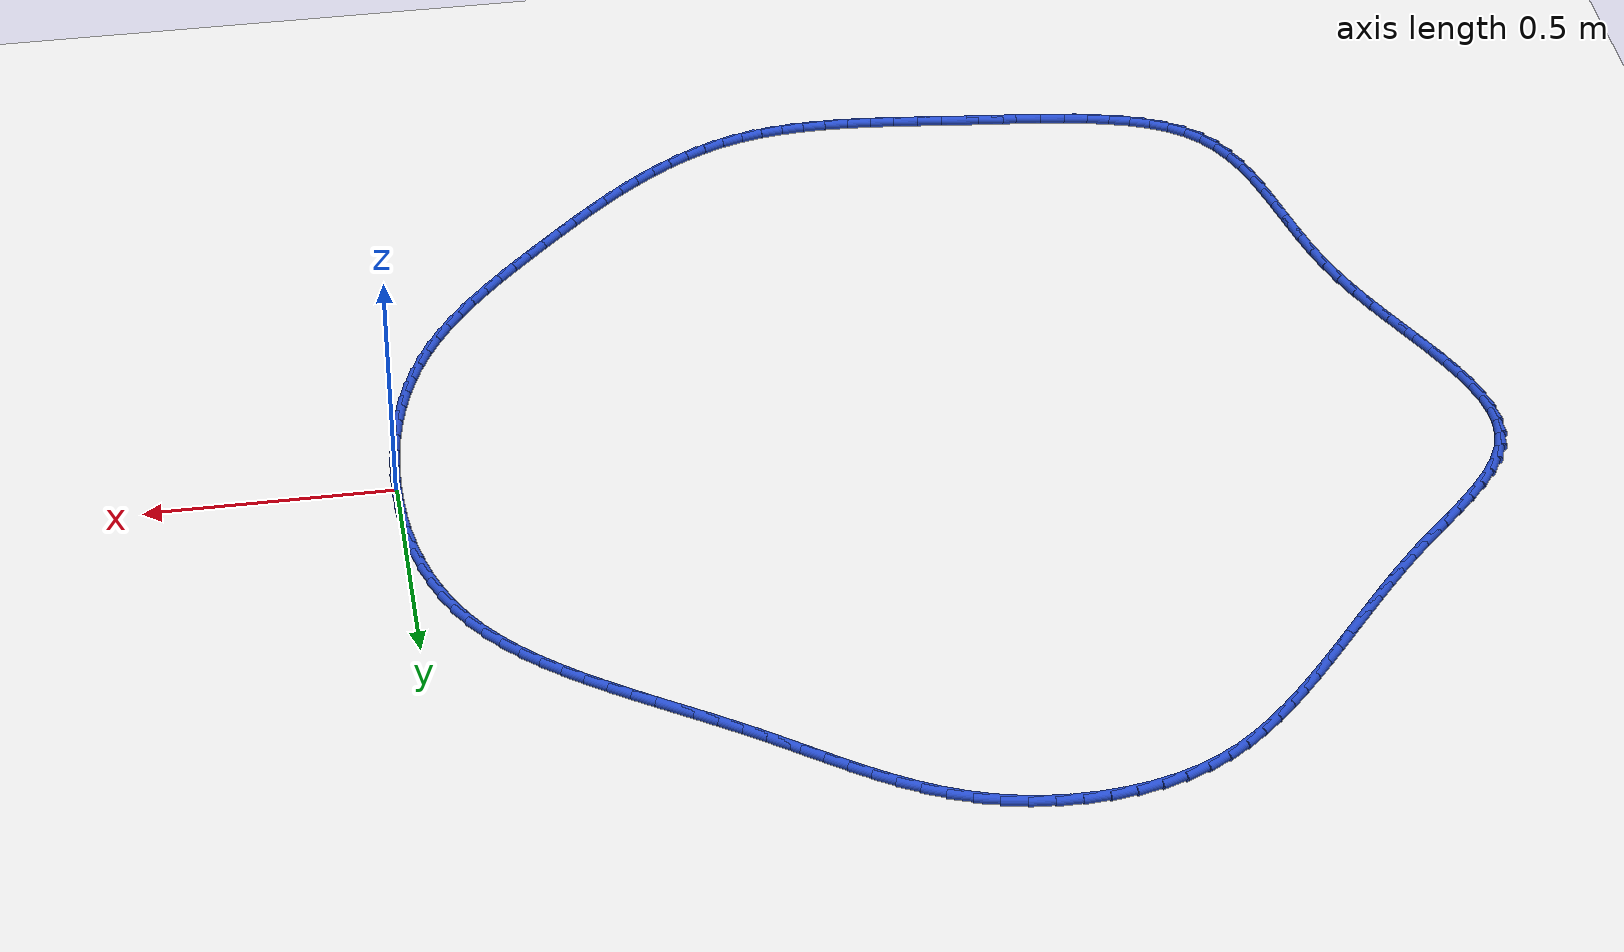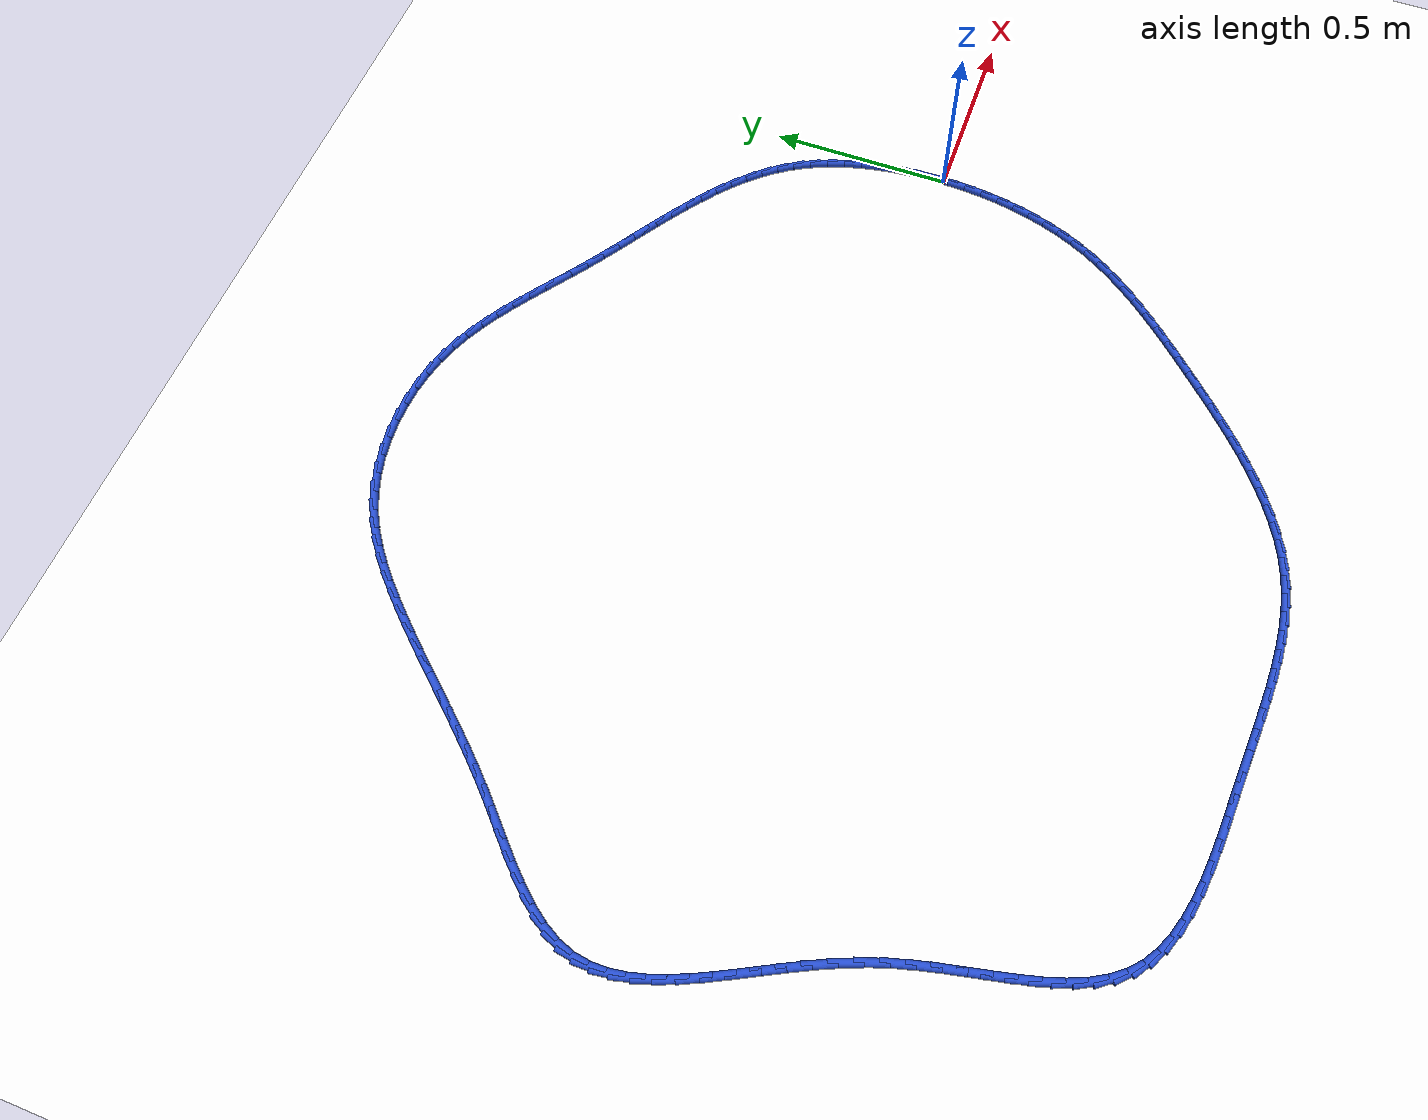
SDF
<sdf version="1.6">
 <world name="default">
  <light name="sun" type="directional">
   <pose>0 0 10 0 -0 0</pose>
   <diffuse>0.8 0.8 0.8 1</diffuse>
   <specular>0.2 0.2 0.2 1</specular>
   <attenuation>
    <range>1000</range>
    <constant>0.9</constant>
    <linear>0.01</linear>
    <quadratic>0.001</quadratic>
   </attenuation>
   <direction>-0.5 0.1 -0.9</direction>
  </light>
  <model name="ground_plane">
   <static>1</static>
   <link name="link">
    <collision name="collision">
     <geometry><plane><normal>0 0 1</normal><size>100 100</size></plane></geometry>
     <surface><friction><ode><mu>100</mu><mu2>50</mu2></ode></friction></surface>
    </collision>
    <visual name="visual">
     <cast_shadows>0</cast_shadows>
     <geometry><plane><normal>0 0 1</normal><size>100 100</size></plane></geometry>
     <material>
      <script><uri>file://media/materials/scripts/gazebo.material</uri><name>Gazebo/WhiteGlow</name></script>
     </material>
    </visual>
   </link>
  </model>
  <gravity>0 0 -9.8</gravity>
  <magnetic_field>6e-06 2.3e-05 -4.2e-05</magnetic_field>
  <atmosphere type="adiabatic"/>
  <physics name="default_physics" default="0" type="ode">
   <max_step_size>0.001</max_step_size>
   <real_time_factor>1</real_time_factor>
   <real_time_update_rate>1000</real_time_update_rate>
  </physics>
  <scene><ambient>0.4 0.4 0.4 1</ambient><background>0.7 0.7 0.7 1</background><shadows>1</shadows></scene>
  <spherical_coordinates>
   <surface_model>EARTH_WGS84</surface_model>
   <latitude_deg>0</latitude_deg>
   <longitude_deg>0</longitude_deg>
   <elevation>0</elevation>
   <heading_deg>0</heading_deg>
  </spherical_coordinates>
  <model name="line">
   <link name="link_0">
    <pose>2.6020852139652106e-17 5.551115123125783e-17 0.01 0 1.57 -1.5619485043957753</pose>
    <collision name="collision">
     <geometry><cylinder><radius>0.01</radius><length>0.08</length></cylinder></geometry>
    </collision>
    <visual name="visual">
     <material>
      <script><name>Gazebo/Blue</name><uri>file://media/materials/scripts/gazebo.material</uri></script>
     </material>
     <geometry><cylinder><radius>0.01</radius><length>0.08</length></cylinder></geometry>
    </visual>
   </link>
   <link name="link_1">
    <pose>-0.00045022236933538456 0.050883776885256846 0.01 0 1.57 -1.5179258800553068</pose>
    <collision name="collision">
     <geometry><cylinder><radius>0.01</radius><length>0.08</length></cylinder></geometry>
    </collision>
    <visual name="visual">
     <material>
      <script><name>Gazebo/Blue</name><uri>file://media/materials/scripts/gazebo.material</uri></script>
     </material>
     <geometry><cylinder><radius>0.01</radius><length>0.08</length></cylinder></geometry>
    </visual>
   </link>
   <link name="link_2">
    <pose>-0.003139674134285478 0.1017050870169513 0.01 0 1.57 -1.4705431116117427</pose>
    <collision name="collision">
     <geometry><cylinder><radius>0.01</radius><length>0.08</length></cylinder></geometry>
    </collision>
    <visual name="visual">
     <material>
      <script><name>Gazebo/Blue</name><uri>file://media/materials/scripts/gazebo.material</uri></script>
     </material>
     <geometry><cylinder><radius>0.01</radius><length>0.08</length></cylinder></geometry>
    </visual>
   </link>
   <link name="link_3">
    <pose>-0.00821534779071211 0.15216389314239184 0.01 0 1.57 -1.4191687556872987</pose>
    <collision name="collision">
     <geometry><cylinder><radius>0.01</radius><length>0.08</length></cylinder></geometry>
    </collision>
    <visual name="visual">
     <material>
      <script><name>Gazebo/Blue</name><uri>file://media/materials/scripts/gazebo.material</uri></script>
     </material>
     <geometry><cylinder><radius>0.01</radius><length>0.08</length></cylinder></geometry>
    </visual>
   </link>
   <link name="link_4">
    <pose>-0.01582423583447712 0.2019601580088869 0.01 0 1.57 -1.3631369850084192</pose>
    <collision name="collision">
     <geometry><cylinder><radius>0.01</radius><length>0.08</length></cylinder></geometry>
    </collision>
    <visual name="visual">
     <material>
      <script><name>Gazebo/Blue</name><uri>file://media/materials/scripts/gazebo.material</uri></script>
     </material>
     <geometry><cylinder><radius>0.01</radius><length>0.08</length></cylinder></geometry>
    </visual>
   </link>
   <link name="link_5">
    <pose>-0.02611333076144237 0.25079384436374497 0.01 0 1.57 -1.3017608858675596</pose>
    <collision name="collision">
     <geometry><cylinder><radius>0.01</radius><length>0.08</length></cylinder></geometry>
    </collision>
    <visual name="visual">
     <material>
      <script><name>Gazebo/Blue</name><uri>file://media/materials/scripts/gazebo.material</uri></script>
     </material>
     <geometry><cylinder><radius>0.01</radius><length>0.08</length></cylinder></geometry>
    </visual>
   </link>
   <link name="link_6">
    <pose>-0.039229625067469714 0.2983649149542743 0.01 0 1.57 -1.2343627922332197</pose>
    <collision name="collision">
     <geometry><cylinder><radius>0.01</radius><length>0.08</length></cylinder></geometry>
    </collision>
    <visual name="visual">
     <material>
      <script><name>Gazebo/Blue</name><uri>file://media/materials/scripts/gazebo.material</uri></script>
     </material>
     <geometry><cylinder><radius>0.01</radius><length>0.08</length></cylinder></geometry>
    </visual>
   </link>
   <link name="link_7">
    <pose>-0.05532011124842101 0.3443733325277836 0.01 0 1.57 -1.1603284807588692</pose>
    <collision name="collision">
     <geometry><cylinder><radius>0.01</radius><length>0.08</length></cylinder></geometry>
    </collision>
    <visual name="visual">
     <material>
      <script><name>Gazebo/Blue</name><uri>file://media/materials/scripts/gazebo.material</uri></script>
     </material>
     <geometry><cylinder><radius>0.01</radius><length>0.08</length></cylinder></geometry>
    </visual>
   </link>
   <link name="link_8">
    <pose>-0.07453178180015811 0.3885190598315812 0.01 0 1.57 -1.0791915962113092</pose>
    <collision name="collision">
     <geometry><cylinder><radius>0.01</radius><length>0.08</length></cylinder></geometry>
    </collision>
    <visual name="visual">
     <material>
      <script><name>Gazebo/Blue</name><uri>file://media/materials/scripts/gazebo.material</uri></script>
     </material>
     <geometry><cylinder><radius>0.01</radius><length>0.08</length></cylinder></geometry>
    </visual>
   </link>
   <link name="link_9">
    <pose>-0.09701162921854284 0.43050205961297533 0.01 0 1.57 -0.992655646375856</pose>
    <collision name="collision">
     <geometry><cylinder><radius>0.01</radius><length>0.08</length></cylinder></geometry>
    </collision>
    <visual name="visual">
     <material>
      <script><name>Gazebo/Blue</name><uri>file://media/materials/scripts/gazebo.material</uri></script>
     </material>
     <geometry><cylinder><radius>0.01</radius><length>0.08</length></cylinder></geometry>
    </visual>
   </link>
   <link name="link_10">
    <pose>-0.12284549626768587 0.47009332811488547 0.01 0 1.57 -0.9110749012230361</pose>
    <collision name="collision">
     <geometry><cylinder><radius>0.01</radius><length>0.08</length></cylinder></geometry>
    </collision>
    <visual name="visual">
     <material>
      <script><name>Gazebo/Blue</name><uri>file://media/materials/scripts/gazebo.material</uri></script>
     </material>
     <geometry><cylinder><radius>0.01</radius><length>0.08</length></cylinder></geometry>
    </visual>
   </link>
   <link name="link_11">
    <pose>-0.15180507192361753 0.5074287927269041 0.01 0 1.57 -0.8386515433862962</pose>
    <collision name="collision">
     <geometry><cylinder><radius>0.01</radius><length>0.08</length></cylinder></geometry>
    </collision>
    <visual name="visual">
     <material>
      <script><name>Gazebo/Blue</name><uri>file://media/materials/scripts/gazebo.material</uri></script>
     </material>
     <geometry><cylinder><radius>0.01</radius><length>0.08</length></cylinder></geometry>
    </visual>
   </link>
   <link name="link_12">
    <pose>-0.18356143931973953 0.5427612478219469 0.01 0 1.57 -0.7759317423718946</pose>
    <collision name="collision">
     <geometry><cylinder><radius>0.01</radius><length>0.08</length></cylinder></geometry>
    </collision>
    <visual name="visual">
     <material>
      <script><name>Gazebo/Blue</name><uri>file://media/materials/scripts/gazebo.material</uri></script>
     </material>
     <geometry><cylinder><radius>0.01</radius><length>0.08</length></cylinder></geometry>
    </visual>
   </link>
   <link name="link_13">
    <pose>-0.21778563608416898 0.5763435406333322 0.01 0 1.57 -0.7229781396319033</pose>
    <collision name="collision">
     <geometry><cylinder><radius>0.01</radius><length>0.08</length></cylinder></geometry>
    </collision>
    <visual name="visual">
     <material>
      <script><name>Gazebo/Blue</name><uri>file://media/materials/scripts/gazebo.material</uri></script>
     </material>
     <geometry><cylinder><radius>0.01</radius><length>0.08</length></cylinder></geometry>
    </visual>
   </link>
   <link name="link_14">
    <pose>-0.2541486998450228 0.608428518394378 0.01 0 1.57 -0.6795485020725676</pose>
    <collision name="collision">
     <geometry><cylinder><radius>0.01</radius><length>0.08</length></cylinder></geometry>
    </collision>
    <visual name="visual">
     <material>
      <script><name>Gazebo/Blue</name><uri>file://media/materials/scripts/gazebo.material</uri></script>
     </material>
     <geometry><cylinder><radius>0.01</radius><length>0.08</length></cylinder></geometry>
    </visual>
   </link>
   <link name="link_15">
    <pose>-0.2923216682304182 0.6392690283384027 0.01 0 1.57 -0.6452492593649483</pose>
    <collision name="collision">
     <geometry><cylinder><radius>0.01</radius><length>0.08</length></cylinder></geometry>
    </collision>
    <visual name="visual">
     <material>
      <script><name>Gazebo/Blue</name><uri>file://media/materials/scripts/gazebo.material</uri></script>
     </material>
     <geometry><cylinder><radius>0.01</radius><length>0.08</length></cylinder></geometry>
    </visual>
   </link>
   <link name="link_16">
    <pose>-0.3319755788684721 0.6691179176987249 0.01 0 1.57 -0.6196496589792518</pose>
    <collision name="collision">
     <geometry><cylinder><radius>0.01</radius><length>0.08</length></cylinder></geometry>
    </collision>
    <visual name="visual">
     <material>
      <script><name>Gazebo/Blue</name><uri>file://media/materials/scripts/gazebo.material</uri></script>
     </material>
     <geometry><cylinder><radius>0.01</radius><length>0.08</length></cylinder></geometry>
    </visual>
   </link>
   <link name="link_17">
    <pose>-0.3727814693873016 0.6982280337086626 0.01 0 1.57 -0.6023577385974448</pose>
    <collision name="collision">
     <geometry><cylinder><radius>0.01</radius><length>0.08</length></cylinder></geometry>
    </collision>
    <visual name="visual">
     <material>
      <script><name>Gazebo/Blue</name><uri>file://media/materials/scripts/gazebo.material</uri></script>
     </material>
     <geometry><cylinder><radius>0.01</radius><length>0.08</length></cylinder></geometry>
    </visual>
   </link>
   <link name="link_18">
    <pose>-0.41441037741502357 0.726852223601534 0.01 0 1.57 -0.5930661751747036</pose>
    <collision name="collision">
     <geometry><cylinder><radius>0.01</radius><length>0.08</length></cylinder></geometry>
    </collision>
    <visual name="visual">
     <material>
      <script><name>Gazebo/Blue</name><uri>file://media/materials/scripts/gazebo.material</uri></script>
     </material>
     <geometry><cylinder><radius>0.01</radius><length>0.08</length></cylinder></geometry>
    </visual>
   </link>
   <link name="link_19">
    <pose>-0.45653334057975514 0.7552433346106575 0.01 0 1.57 -0.5915767664310219</pose>
    <collision name="collision">
     <geometry><cylinder><radius>0.01</radius><length>0.08</length></cylinder></geometry>
    </collision>
    <visual name="visual">
     <material>
      <script><name>Gazebo/Blue</name><uri>file://media/materials/scripts/gazebo.material</uri></script>
     </material>
     <geometry><cylinder><radius>0.01</radius><length>0.08</length></cylinder></geometry>
    </visual>
   </link>
   <link name="link_20">
    <pose>-0.49882139650961355 0.7836542139693515 0.01 0 1.57 -0.5978102601333636</pose>
    <collision name="collision">
     <geometry><cylinder><radius>0.01</radius><length>0.08</length></cylinder></geometry>
    </collision>
    <visual name="visual">
     <material>
      <script><name>Gazebo/Blue</name><uri>file://media/materials/scripts/gazebo.material</uri></script>
     </material>
     <geometry><cylinder><radius>0.01</radius><length>0.08</length></cylinder></geometry>
    </visual>
   </link>
   <link name="link_21">
    <pose>-0.5409455828327155 0.8123377089109345 0.01 0 1.57 -0.6118054143662642</pose>
    <collision name="collision">
     <geometry><cylinder><radius>0.01</radius><length>0.08</length></cylinder></geometry>
    </collision>
    <visual name="visual">
     <material>
      <script><name>Gazebo/Blue</name><uri>file://media/materials/scripts/gazebo.material</uri></script>
     </material>
     <geometry><cylinder><radius>0.01</radius><length>0.08</length></cylinder></geometry>
    </visual>
   </link>
   <link name="link_22">
    <pose>-0.5825769371771782 0.8415466666687241 0.01 0 1.57 -0.6324138514529687</pose>
    <collision name="collision">
     <geometry><cylinder><radius>0.01</radius><length>0.08</length></cylinder></geometry>
    </collision>
    <visual name="visual">
     <material>
      <script><name>Gazebo/Blue</name><uri>file://media/materials/scripts/gazebo.material</uri></script>
     </material>
     <geometry><cylinder><radius>0.01</radius><length>0.08</length></cylinder></geometry>
    </visual>
   </link>
   <link name="link_23">
    <pose>-0.62342885115673 0.8714836980309244 0.01 0 1.57 -0.6478183711299126</pose>
    <collision name="collision">
     <geometry><cylinder><radius>0.01</radius><length>0.08</length></cylinder></geometry>
    </collision>
    <visual name="visual">
     <material>
      <script><name>Gazebo/Blue</name><uri>file://media/materials/scripts/gazebo.material</uri></script>
     </material>
     <geometry><cylinder><radius>0.01</radius><length>0.08</length></cylinder></geometry>
    </visual>
   </link>
   <link name="link_24">
    <pose>-0.6636054045381286 0.9018880150365185 0.01 0 1.57 -0.6514661691283802</pose>
    <collision name="collision">
     <geometry><cylinder><radius>0.01</radius><length>0.08</length></cylinder></geometry>
    </collision>
    <visual name="visual">
     <material>
      <script><name>Gazebo/Blue</name><uri>file://media/materials/scripts/gazebo.material</uri></script>
     </material>
     <geometry><cylinder><radius>0.01</radius><length>0.08</length></cylinder></geometry>
    </visual>
   </link>
   <link name="link_25">
    <pose>-0.7034215862405832 0.9322486684726404 0.01 0 1.57 -0.6430819737672484</pose>
    <collision name="collision">
     <geometry><cylinder><radius>0.01</radius><length>0.08</length></cylinder></geometry>
    </collision>
    <visual name="visual">
     <material>
      <script><name>Gazebo/Blue</name><uri>file://media/materials/scripts/gazebo.material</uri></script>
     </material>
     <geometry><cylinder><radius>0.01</radius><length>0.08</length></cylinder></geometry>
    </visual>
   </link>
   <link name="link_26">
    <pose>-0.7431944410824836 0.9620522706058242 0.01 0 1.57 -0.6223704616174938</pose>
    <collision name="collision">
     <geometry><cylinder><radius>0.01</radius><length>0.08</length></cylinder></geometry>
    </collision>
    <visual name="visual">
     <material>
      <script><name>Gazebo/Blue</name><uri>file://media/materials/scripts/gazebo.material</uri></script>
     </material>
     <geometry><cylinder><radius>0.01</radius><length>0.08</length></cylinder></geometry>
    </visual>
   </link>
   <link name="link_27">
    <pose>-0.7832410138822201 0.9907854337026043 0.01 0 1.57 -0.5889862997316119</pose>
    <collision name="collision">
     <geometry><cylinder><radius>0.01</radius><length>0.08</length></cylinder></geometry>
    </collision>
    <visual name="visual">
     <material>
      <script><name>Gazebo/Blue</name><uri>file://media/materials/scripts/gazebo.material</uri></script>
     </material>
     <geometry><cylinder><radius>0.01</radius><length>0.08</length></cylinder></geometry>
    </visual>
   </link>
   <link name="link_28">
    <pose>-0.8238783494581836 1.0179347700295154 0.01 0 1.57 -0.5426295327525729</pose>
    <collision name="collision">
     <geometry><cylinder><radius>0.01</radius><length>0.08</length></cylinder></geometry>
    </collision>
    <visual name="visual">
     <material>
      <script><name>Gazebo/Blue</name><uri>file://media/materials/scripts/gazebo.material</uri></script>
     </material>
     <geometry><cylinder><radius>0.01</radius><length>0.08</length></cylinder></geometry>
    </visual>
   </link>
   <link name="link_29">
    <pose>-0.8654234926287635 1.0429868918530916 0.01 0 1.57 -0.4832136802849587</pose>
    <collision name="collision">
     <geometry><cylinder><radius>0.01</radius><length>0.08</length></cylinder></geometry>
    </collision>
    <visual name="visual">
     <material>
      <script><name>Gazebo/Blue</name><uri>file://media/materials/scripts/gazebo.material</uri></script>
     </material>
     <geometry><cylinder><radius>0.01</radius><length>0.08</length></cylinder></geometry>
    </visual>
   </link>
   <link name="link_30">
    <pose>-0.9081934882123504 1.0654284114398669 0.01 0 1.57 -0.4111041655468128</pose>
    <collision name="collision">
     <geometry><cylinder><radius>0.01</radius><length>0.08</length></cylinder></geometry>
    </collision>
    <visual name="visual">
     <material>
      <script><name>Gazebo/Blue</name><uri>file://media/materials/scripts/gazebo.material</uri></script>
     </material>
     <geometry><cylinder><radius>0.01</radius><length>0.08</length></cylinder></geometry>
    </visual>
   </link>
   <link name="link_31">
    <pose>-0.9525053810273342 1.084745941056376 0.01 0 1.57 -0.3274119269679063</pose>
    <collision name="collision">
     <geometry><cylinder><radius>0.01</radius><length>0.08</length></cylinder></geometry>
    </collision>
    <visual name="visual">
     <material>
      <script><name>Gazebo/Blue</name><uri>file://media/materials/scripts/gazebo.material</uri></script>
     </material>
     <geometry><cylinder><radius>0.01</radius><length>0.08</length></cylinder></geometry>
    </visual>
   </link>
   <link name="link_32">
    <pose>-0.9986749371279814 1.1004267709305726 0.01 0 1.57 -0.23794957068730055</pose>
    <collision name="collision">
     <geometry><cylinder><radius>0.01</radius><length>0.08</length></cylinder></geometry>
    </collision>
    <visual name="visual">
     <material>
      <script><name>Gazebo/Blue</name><uri>file://media/materials/scripts/gazebo.material</uri></script>
     </material>
     <geometry><cylinder><radius>0.01</radius><length>0.08</length></cylinder></geometry>
    </visual>
   </link>
   <link name="link_33">
    <pose>-1.046766978245515 1.1120912342545275 0.01 0 1.57 -0.15147222430488186</pose>
    <collision name="collision">
     <geometry><cylinder><radius>0.01</radius><length>0.08</length></cylinder></geometry>
    </collision>
    <visual name="visual">
     <material>
      <script><name>Gazebo/Blue</name><uri>file://media/materials/scripts/gazebo.material</uri></script>
     </material>
     <geometry><cylinder><radius>0.01</radius><length>0.08</length></cylinder></geometry>
    </visual>
   </link>
   <link name="link_34">
    <pose>-1.0962960239960349 1.1196514174812258 0.01 0 1.57 -0.06748028130849294</pose>
    <collision name="collision">
     <geometry><cylinder><radius>0.01</radius><length>0.08</length></cylinder></geometry>
    </collision>
    <visual name="visual">
     <material>
      <script><name>Gazebo/Blue</name><uri>file://media/materials/scripts/gazebo.material</uri></script>
     </material>
     <geometry><cylinder><radius>0.01</radius><length>0.08</length></cylinder></geometry>
    </visual>
   </link>
   <link name="link_35">
    <pose>-1.1467035981388418 1.123058107222472 0.01 0 1.57 0.015690696835988168</pose>
    <collision name="collision">
     <geometry><cylinder><radius>0.01</radius><length>0.08</length></cylinder></geometry>
    </collision>
    <visual name="visual">
     <material>
      <script><name>Gazebo/Blue</name><uri>file://media/materials/scripts/gazebo.material</uri></script>
     </material>
     <geometry><cylinder><radius>0.01</radius><length>0.08</length></cylinder></geometry>
    </visual>
   </link>
   <link name="link_36">
    <pose>-1.1974312244332377 1.1222620900900717 0.01 0 1.57 0.09964937911850397</pose>
    <collision name="collision">
     <geometry><cylinder><radius>0.01</radius><length>0.08</length></cylinder></geometry>
    </collision>
    <visual name="visual">
     <material>
      <script><name>Gazebo/Blue</name><uri>file://media/materials/scripts/gazebo.material</uri></script>
     </material>
     <geometry><cylinder><radius>0.01</radius><length>0.08</length></cylinder></geometry>
    </visual>
   </link>
   <link name="link_37">
    <pose>-1.2479204266385242 1.1172141526958304 0.01 0 1.57 0.1859653915850451</pose>
    <collision name="collision">
     <geometry><cylinder><radius>0.01</radius><length>0.08</length></cylinder></geometry>
    </collision>
    <visual name="visual">
     <material>
      <script><name>Gazebo/Blue</name><uri>file://media/materials/scripts/gazebo.material</uri></script>
     </material>
     <geometry><cylinder><radius>0.01</radius><length>0.08</length></cylinder></geometry>
    </visual>
   </link>
   <link name="link_38">
    <pose>-1.2976127285140013 1.1078650816515525 0.01 0 1.57 0.27617277642183796</pose>
    <collision name="collision">
     <geometry><cylinder><radius>0.01</radius><length>0.08</length></cylinder></geometry>
    </collision>
    <visual name="visual">
     <material>
      <script><name>Gazebo/Blue</name><uri>file://media/materials/scripts/gazebo.material</uri></script>
     </material>
     <geometry><cylinder><radius>0.01</radius><length>0.08</length></cylinder></geometry>
    </visual>
   </link>
   <link name="link_39">
    <pose>-1.3459496538189715 1.0941656635690433 0.01 0 1.57 0.3717435163472172</pose>
    <collision name="collision">
     <geometry><cylinder><radius>0.01</radius><length>0.08</length></cylinder></geometry>
    </collision>
    <visual name="visual">
     <material>
      <script><name>Gazebo/Blue</name><uri>file://media/materials/scripts/gazebo.material</uri></script>
     </material>
     <geometry><cylinder><radius>0.01</radius><length>0.08</length></cylinder></geometry>
    </visual>
   </link>
   <link name="link_40">
    <pose>-1.3923727263127352 1.0760666850601077 0.01 0 1.57 0.4737704807292046</pose>
    <collision name="collision">
     <geometry><cylinder><radius>0.01</radius><length>0.08</length></cylinder></geometry>
    </collision>
    <visual name="visual">
     <material>
      <script><name>Gazebo/Blue</name><uri>file://media/materials/scripts/gazebo.material</uri></script>
     </material>
     <geometry><cylinder><radius>0.01</radius><length>0.08</length></cylinder></geometry>
    </visual>
   </link>
   <link name="link_41">
    <pose>-1.4363328076587616 1.0535275426008113 0.01 0 1.57 0.5736998329180988</pose>
    <collision name="collision">
     <geometry><cylinder><radius>0.01</radius><length>0.08</length></cylinder></geometry>
    </collision>
    <visual name="visual">
     <material>
      <script><name>Gazebo/Blue</name><uri>file://media/materials/scripts/gazebo.material</uri></script>
     </material>
     <geometry><cylinder><radius>0.01</radius><length>0.08</length></cylinder></geometry>
    </visual>
   </link>
   <link name="link_42">
    <pose>-1.4776374078307344 1.0268364745020435 0.01 0 1.57 0.6588415193146527</pose>
    <collision name="collision">
     <geometry><cylinder><radius>0.01</radius><length>0.08</length></cylinder></geometry>
    </collision>
    <visual name="visual">
     <material>
      <script><name>Gazebo/Blue</name><uri>file://media/materials/scripts/gazebo.material</uri></script>
     </material>
     <geometry><cylinder><radius>0.01</radius><length>0.08</length></cylinder></geometry>
    </visual>
   </link>
   <link name="link_43">
    <pose>-1.516553687885951 0.9967055329590829 0.01 0 1.57 0.7281121211325399</pose>
    <collision name="collision">
     <geometry><cylinder><radius>0.01</radius><length>0.08</length></cylinder></geometry>
    </collision>
    <visual name="visual">
     <material>
      <script><name>Gazebo/Blue</name><uri>file://media/materials/scripts/gazebo.material</uri></script>
     </material>
     <geometry><cylinder><radius>0.01</radius><length>0.08</length></cylinder></geometry>
    </visual>
   </link>
   <link name="link_44">
    <pose>-1.5533791639401537 0.9638747585603372 0.01 0 1.57 0.78193767921994</pose>
    <collision name="collision">
     <geometry><cylinder><radius>0.01</radius><length>0.08</length></cylinder></geometry>
    </collision>
    <visual name="visual">
     <material>
      <script><name>Gazebo/Blue</name><uri>file://media/materials/scripts/gazebo.material</uri></script>
     </material>
     <geometry><cylinder><radius>0.01</radius><length>0.08</length></cylinder></geometry>
    </visual>
   </link>
   <link name="link_45">
    <pose>-1.588411352109083 0.929084191894214 0.01 0 1.57 0.8209549626306731</pose>
    <collision name="collision">
     <geometry><cylinder><radius>0.01</radius><length>0.08</length></cylinder></geometry>
    </collision>
    <visual name="visual">
     <material>
      <script><name>Gazebo/Blue</name><uri>file://media/materials/scripts/gazebo.material</uri></script>
     </material>
     <geometry><cylinder><radius>0.01</radius><length>0.08</length></cylinder></geometry>
    </visual>
   </link>
   <link name="link_46">
    <pose>-1.6219477685084809 0.8930738735491202 0.01 0 1.57 0.8464739829932372</pose>
    <collision name="collision">
     <geometry><cylinder><radius>0.01</radius><length>0.08</length></cylinder></geometry>
    </collision>
    <visual name="visual">
     <material>
      <script><name>Gazebo/Blue</name><uri>file://media/materials/scripts/gazebo.material</uri></script>
     </material>
     <geometry><cylinder><radius>0.01</radius><length>0.08</length></cylinder></geometry>
    </visual>
   </link>
   <link name="link_47">
    <pose>-1.6542833155912806 0.8565259745186992 0.01 0 1.57 0.8648333495760041</pose>
    <collision name="collision">
     <geometry><cylinder><radius>0.01</radius><length>0.08</length></cylinder></geometry>
    </collision>
    <visual name="visual">
     <material>
      <script><name>Gazebo/Blue</name><uri>file://media/materials/scripts/gazebo.material</uri></script>
     </material>
     <geometry><cylinder><radius>0.01</radius><length>0.08</length></cylinder></geometry>
    </visual>
   </link>
   <link name="link_48">
    <pose>-1.6856930455960712 0.8196831585056136 0.01 0 1.57 0.8786747877065457</pose>
    <collision name="collision">
     <geometry><cylinder><radius>0.01</radius><length>0.08</length></cylinder></geometry>
    </collision>
    <visual name="visual">
     <material>
      <script><name>Gazebo/Blue</name><uri>file://media/materials/scripts/gazebo.material</uri></script>
     </material>
     <geometry><cylinder><radius>0.01</radius><length>0.08</length></cylinder></geometry>
    </visual>
   </link>
   <link name="link_49">
    <pose>-1.716442900656303 0.7825863806788251 0.01 0 1.57 0.8878211881460114</pose>
    <collision name="collision">
     <geometry><cylinder><radius>0.01</radius><length>0.08</length></cylinder></geometry>
    </collision>
    <visual name="visual">
     <material>
      <script><name>Gazebo/Blue</name><uri>file://media/materials/scripts/gazebo.material</uri></script>
     </material>
     <geometry><cylinder><radius>0.01</radius><length>0.08</length></cylinder></geometry>
    </visual>
   </link>
   <link name="link_50">
    <pose>-1.7467987751618146 0.7452755391070678 0.01 0 1.57 0.8921670746372405</pose>
    <collision name="collision">
     <geometry><cylinder><radius>0.01</radius><length>0.08</length></cylinder></geometry>
    </collision>
    <visual name="visual">
     <material>
      <script><name>Gazebo/Blue</name><uri>file://media/materials/scripts/gazebo.material</uri></script>
     </material>
     <geometry><cylinder><radius>0.01</radius><length>0.08</length></cylinder></geometry>
    </visual>
   </link>
   <link name="link_51">
    <pose>-1.7770265635024443 0.7077905318590765 0.01 0 1.57 0.8916915124959313</pose>
    <collision name="collision">
     <geometry><cylinder><radius>0.01</radius><length>0.08</length></cylinder></geometry>
    </collision>
    <visual name="visual">
     <material>
      <script><name>Gazebo/Blue</name><uri>file://media/materials/scripts/gazebo.material</uri></script>
     </material>
     <geometry><cylinder><radius>0.01</radius><length>0.08</length></cylinder></geometry>
    </visual>
   </link>
   <link name="link_52">
    <pose>-1.8073921600680296 0.6701712570035844 0.01 0 1.57 0.8864552870526387</pose>
    <collision name="collision">
     <geometry><cylinder><radius>0.01</radius><length>0.08</length></cylinder></geometry>
    </collision>
    <visual name="visual">
     <material>
      <script><name>Gazebo/Blue</name><uri>file://media/materials/scripts/gazebo.material</uri></script>
     </material>
     <geometry><cylinder><radius>0.01</radius><length>0.08</length></cylinder></geometry>
    </visual>
   </link>
   <link name="link_53">
    <pose>-1.8381614592484097 0.6324576126093272 0.01 0 1.57 0.8765979163526821</pose>
    <collision name="collision">
     <geometry><cylinder><radius>0.01</radius><length>0.08</length></cylinder></geometry>
    </collision>
    <visual name="visual">
     <material>
      <script><name>Gazebo/Blue</name><uri>file://media/materials/scripts/gazebo.material</uri></script>
     </material>
     <geometry><cylinder><radius>0.01</radius><length>0.08</length></cylinder></geometry>
    </visual>
   </link>
   <link name="link_54">
    <pose>-1.8696003554334213 0.594689496745038 0.01 0 1.57 0.8623344723722596</pose>
    <collision name="collision">
     <geometry><cylinder><radius>0.01</radius><length>0.08</length></cylinder></geometry>
    </collision>
    <visual name="visual">
     <material>
      <script><name>Gazebo/Blue</name><uri>file://media/materials/scripts/gazebo.material</uri></script>
     </material>
     <geometry><cylinder><radius>0.01</radius><length>0.08</length></cylinder></geometry>
    </visual>
   </link>
   <link name="link_55">
    <pose>-1.9019747430129041 0.5569068074794515 0.01 0 1.57 0.8439517524783946</pose>
    <collision name="collision">
     <geometry><cylinder><radius>0.01</radius><length>0.08</length></cylinder></geometry>
    </collision>
    <visual name="visual">
     <material>
      <script><name>Gazebo/Blue</name><uri>file://media/materials/scripts/gazebo.material</uri></script>
     </material>
     <geometry><cylinder><radius>0.01</radius><length>0.08</length></cylinder></geometry>
    </visual>
   </link>
   <link name="link_56">
    <pose>-1.9355505163766946 0.5191494428813023 0.01 0 1.57 0.8218210334294972</pose>
    <collision name="collision">
     <geometry><cylinder><radius>0.01</radius><length>0.08</length></cylinder></geometry>
    </collision>
    <visual name="visual">
     <material>
      <script><name>Gazebo/Blue</name><uri>file://media/materials/scripts/gazebo.material</uri></script>
     </material>
     <geometry><cylinder><radius>0.01</radius><length>0.08</length></cylinder></geometry>
    </visual>
   </link>
   <link name="link_57">
    <pose>-1.970592430051945 0.4814571692391648 0.01 0 1.57 0.8022392510476235</pose>
    <collision name="collision">
     <geometry><cylinder><radius>0.01</radius><length>0.08</length></cylinder></geometry>
    </collision>
    <visual name="visual">
     <material>
      <script><name>Gazebo/Blue</name><uri>file://media/materials/scripts/gazebo.material</uri></script>
     </material>
     <geometry><cylinder><radius>0.01</radius><length>0.08</length></cylinder></geometry>
    </visual>
   </link>
   <link name="link_58">
    <pose>-2.0069779628043185 0.44382497967550927 0.01 0 1.57 0.7992518953064738</pose>
    <collision name="collision">
     <geometry><cylinder><radius>0.01</radius><length>0.08</length></cylinder></geometry>
    </collision>
    <visual name="visual">
     <material>
      <script><name>Gazebo/Blue</name><uri>file://media/materials/scripts/gazebo.material</uri></script>
     </material>
     <geometry><cylinder><radius>0.01</radius><length>0.08</length></cylinder></geometry>
    </visual>
   </link>
   <link name="link_59">
    <pose>-2.0436348682296583 0.4061380690578862 0.01 0 1.57 0.8147411020660419</pose>
    <collision name="collision">
     <geometry><cylinder><radius>0.01</radius><length>0.08</length></cylinder></geometry>
    </collision>
    <visual name="visual">
     <material>
      <script><name>Gazebo/Blue</name><uri>file://media/materials/scripts/gazebo.material</uri></script>
     </material>
     <geometry><cylinder><radius>0.01</radius><length>0.08</length></cylinder></geometry>
    </visual>
   </link>
   <link name="link_60">
    <pose>-2.079347977004295 0.3682651088556588 0.01 0 1.57 0.8499293745787677</pose>
    <collision name="collision">
     <geometry><cylinder><radius>0.01</radius><length>0.08</length></cylinder></geometry>
    </collision>
    <visual name="visual">
     <material>
      <script><name>Gazebo/Blue</name><uri>file://media/materials/scripts/gazebo.material</uri></script>
     </material>
     <geometry><cylinder><radius>0.01</radius><length>0.08</length></cylinder></geometry>
    </visual>
   </link>
   <link name="link_61">
    <pose>-2.11290211980456 0.3300747705381895 0.01 0 1.57 0.9077017667727729</pose>
    <collision name="collision">
     <geometry><cylinder><radius>0.01</radius><length>0.08</length></cylinder></geometry>
    </collision>
    <visual name="visual">
     <material>
      <script><name>Gazebo/Blue</name><uri>file://media/materials/scripts/gazebo.material</uri></script>
     </material>
     <geometry><cylinder><radius>0.01</radius><length>0.08</length></cylinder></geometry>
    </visual>
   </link>
   <link name="link_62">
    <pose>-2.1430821273067853 0.291435725574842 0.01 0 1.57 0.9926611179673445</pose>
    <collision name="collision">
     <geometry><cylinder><radius>0.01</radius><length>0.08</length></cylinder></geometry>
    </collision>
    <visual name="visual">
     <material>
      <script><name>Gazebo/Blue</name><uri>file://media/materials/scripts/gazebo.material</uri></script>
     </material>
     <geometry><cylinder><radius>0.01</radius><length>0.08</length></cylinder></geometry>
    </visual>
   </link>
   <link name="link_63">
    <pose>-2.168672830187301 0.25221664543497835 0.01 0 1.57 1.110741239572612</pose>
    <collision name="collision">
     <geometry><cylinder><radius>0.01</radius><length>0.08</length></cylinder></geometry>
    </collision>
    <visual name="visual">
     <material>
      <script><name>Gazebo/Blue</name><uri>file://media/materials/scripts/gazebo.material</uri></script>
     </material>
     <geometry><cylinder><radius>0.01</radius><length>0.08</length></cylinder></geometry>
    </visual>
   </link>
   <link name="link_64">
    <pose>-2.1884590591224393 0.21228620158796227 0.01 0 1.57 1.2662001948275081</pose>
    <collision name="collision">
     <geometry><cylinder><radius>0.01</radius><length>0.08</length></cylinder></geometry>
    </collision>
    <visual name="visual">
     <material>
      <script><name>Gazebo/Blue</name><uri>file://media/materials/scripts/gazebo.material</uri></script>
     </material>
     <geometry><cylinder><radius>0.01</radius><length>0.08</length></cylinder></geometry>
    </visual>
   </link>
   <link name="link_65">
    <pose>-2.2012762340398586 0.17151643268418337 0.01 0 1.57 1.4352474200831318</pose>
    <collision name="collision">
     <geometry><cylinder><radius>0.01</radius><length>0.08</length></cylinder></geometry>
    </collision>
    <visual name="visual">
     <material>
      <script><name>Gazebo/Blue</name><uri>file://media/materials/scripts/gazebo.material</uri></script>
     </material>
     <geometry><cylinder><radius>0.01</radius><length>0.08</length></cylinder></geometry>
    </visual>
   </link>
   <link name="link_66">
    <pose>-2.206959476658566 0.12984591674387888 0.01 0 1.57 -1.554373294129794</pose>
    <collision name="collision">
     <geometry><cylinder><radius>0.01</radius><length>0.08</length></cylinder></geometry>
    </collision>
    <visual name="visual">
     <material>
      <script><name>Gazebo/Blue</name><uri>file://media/materials/scripts/gazebo.material</uri></script>
     </material>
     <geometry><cylinder><radius>0.01</radius><length>0.08</length></cylinder></geometry>
    </visual>
   </link>
   <link name="link_67">
    <pose>-2.2062602574809786 0.0872742232460769 0.01 0 1.57 -1.4269569507696163</pose>
    <collision name="collision">
     <geometry><cylinder><radius>0.01</radius><length>0.08</length></cylinder></geometry>
    </collision>
    <visual name="visual">
     <material>
      <script><name>Gazebo/Blue</name><uri>file://media/materials/scripts/gazebo.material</uri></script>
     </material>
     <geometry><cylinder><radius>0.01</radius><length>0.08</length></cylinder></geometry>
    </visual>
   </link>
   <link name="link_68">
    <pose>-2.1999639260398602 0.04380317663158355 0.01 0 1.57 -1.325479342614116</pose>
    <collision name="collision">
     <geometry><cylinder><radius>0.01</radius><length>0.08</length></cylinder></geometry>
    </collision>
    <visual name="visual">
     <material>
      <script><name>Gazebo/Blue</name><uri>file://media/materials/scripts/gazebo.material</uri></script>
     </material>
     <geometry><cylinder><radius>0.01</radius><length>0.08</length></cylinder></geometry>
    </visual>
   </link>
   <link name="link_69">
    <pose>-2.1888558318679725 -0.0005653986587938614 0.01 0 1.57 -1.2481231924386886</pose>
    <collision name="collision">
     <geometry><cylinder><radius>0.01</radius><length>0.08</length></cylinder></geometry>
    </collision>
    <visual name="visual">
     <material>
      <script><name>Gazebo/Blue</name><uri>file://media/materials/scripts/gazebo.material</uri></script>
     </material>
     <geometry><cylinder><radius>0.01</radius><length>0.08</length></cylinder></geometry>
    </visual>
   </link>
   <link name="link_70">
    <pose>-2.1737213244980786 -0.045829678184249344 0.01 0 1.57 -1.1919288070272918</pose>
    <collision name="collision">
     <geometry><cylinder><radius>0.01</radius><length>0.08</length></cylinder></geometry>
    </collision>
    <visual name="visual">
     <material>
      <script><name>Gazebo/Blue</name><uri>file://media/materials/scripts/gazebo.material</uri></script>
     </material>
     <geometry><cylinder><radius>0.01</radius><length>0.08</length></cylinder></geometry>
    </visual>
   </link>
   <link name="link_71">
    <pose>-2.155345753462942 -0.09198783750397548 0.01 0 1.57 -1.1539913426041732</pose>
    <collision name="collision">
     <geometry><cylinder><radius>0.01</radius><length>0.08</length></cylinder></geometry>
    </collision>
    <visual name="visual">
     <material>
      <script><name>Gazebo/Blue</name><uri>file://media/materials/scripts/gazebo.material</uri></script>
     </material>
     <geometry><cylinder><radius>0.01</radius><length>0.08</length></cylinder></geometry>
    </visual>
   </link>
   <link name="link_72">
    <pose>-2.134514468295323 -0.1390380521771658 0.01 0 1.57 -1.1319542641162077</pose>
    <collision name="collision">
     <geometry><cylinder><radius>0.01</radius><length>0.08</length></cylinder></geometry>
    </collision>
    <visual name="visual">
     <material>
      <script><name>Gazebo/Blue</name><uri>file://media/materials/scripts/gazebo.material</uri></script>
     </material>
     <geometry><cylinder><radius>0.01</radius><length>0.08</length></cylinder></geometry>
    </visual>
   </link>
   <link name="link_73">
    <pose>-2.1120128185279854 -0.18697849776301456 0.01 0 1.57 -1.12412864717959</pose>
    <collision name="collision">
     <geometry><cylinder><radius>0.01</radius><length>0.08</length></cylinder></geometry>
    </collision>
    <visual name="visual">
     <material>
      <script><name>Gazebo/Blue</name><uri>file://media/materials/scripts/gazebo.material</uri></script>
     </material>
     <geometry><cylinder><radius>0.01</radius><length>0.08</length></cylinder></geometry>
    </visual>
   </link>
   <link name="link_74">
    <pose>-2.0886261536936916 -0.23580734982071344 0.01 0 1.57 -1.1294590071449844</pose>
    <collision name="collision">
     <geometry><cylinder><radius>0.01</radius><length>0.08</length></cylinder></geometry>
    </collision>
    <visual name="visual">
     <material>
      <script><name>Gazebo/Blue</name><uri>file://media/materials/scripts/gazebo.material</uri></script>
     </material>
     <geometry><cylinder><radius>0.01</radius><length>0.08</length></cylinder></geometry>
    </visual>
   </link>
   <link name="link_75">
    <pose>-2.0651398233252056 -0.2855227839094565 0.01 0 1.57 -1.1474402667561787</pose>
    <collision name="collision">
     <geometry><cylinder><radius>0.01</radius><length>0.08</length></cylinder></geometry>
    </collision>
    <visual name="visual">
     <material>
      <script><name>Gazebo/Blue</name><uri>file://media/materials/scripts/gazebo.material</uri></script>
     </material>
     <geometry><cylinder><radius>0.01</radius><length>0.08</length></cylinder></geometry>
    </visual>
   </link>
   <link name="link_76">
    <pose>-2.042339176955288 -0.33612297558843707 0.01 0 1.57 -1.178020911487044</pose>
    <collision name="collision">
     <geometry><cylinder><radius>0.01</radius><length>0.08</length></cylinder></geometry>
    </collision>
    <visual name="visual">
     <material>
      <script><name>Gazebo/Blue</name><uri>file://media/materials/scripts/gazebo.material</uri></script>
     </material>
     <geometry><cylinder><radius>0.01</radius><length>0.08</length></cylinder></geometry>
    </visual>
   </link>
   <link name="link_77">
    <pose>-2.021009564116701 -0.3876061004168484 0.01 0 1.57 -1.2214909163250625</pose>
    <collision name="collision">
     <geometry><cylinder><radius>0.01</radius><length>0.08</length></cylinder></geometry>
    </collision>
    <visual name="visual">
     <material>
      <script><name>Gazebo/Blue</name><uri>file://media/materials/scripts/gazebo.material</uri></script>
     </material>
     <geometry><cylinder><radius>0.01</radius><length>0.08</length></cylinder></geometry>
    </visual>
   </link>
   <link name="link_78">
    <pose>-2.0019363343422096 -0.4399703339538847 0.01 0 1.57 -1.275178385361914</pose>
    <collision name="collision">
     <geometry><cylinder><radius>0.01</radius><length>0.08</length></cylinder></geometry>
    </collision>
    <visual name="visual">
     <material>
      <script><name>Gazebo/Blue</name><uri>file://media/materials/scripts/gazebo.material</uri></script>
     </material>
     <geometry><cylinder><radius>0.01</radius><length>0.08</length></cylinder></geometry>
    </visual>
   </link>
   <link name="link_79">
    <pose>-1.9857383310637593 -0.49315852503173924 0.01 0 1.57 -1.3208078573087134</pose>
    <collision name="collision">
     <geometry><cylinder><radius>0.01</radius><length>0.08</length></cylinder></geometry>
    </collision>
    <visual name="visual">
     <material>
      <script><name>Gazebo/Blue</name><uri>file://media/materials/scripts/gazebo.material</uri></script>
     </material>
     <geometry><cylinder><radius>0.01</radius><length>0.08</length></cylinder></geometry>
    </visual>
   </link>
   <link name="link_80">
    <pose>-1.9720458873098967 -0.546785059771894 0.01 0 1.57 -1.3518065181097747</pose>
    <collision name="collision">
     <geometry><cylinder><radius>0.01</radius><length>0.08</length></cylinder></geometry>
    </collision>
    <visual name="visual">
     <material>
      <script><name>Gazebo/Blue</name><uri>file://media/materials/scripts/gazebo.material</uri></script>
     </material>
     <geometry><cylinder><radius>0.01</radius><length>0.08</length></cylinder></geometry>
    </visual>
   </link>
   <link name="link_81">
    <pose>-1.9601259588150635 -0.6003435811143499 0.01 0 1.57 -1.3682480862006308</pose>
    <collision name="collision">
     <geometry><cylinder><radius>0.01</radius><length>0.08</length></cylinder></geometry>
    </collision>
    <visual name="visual">
     <material>
      <script><name>Gazebo/Blue</name><uri>file://media/materials/scripts/gazebo.material</uri></script>
     </material>
     <geometry><cylinder><radius>0.01</radius><length>0.08</length></cylinder></geometry>
    </visual>
   </link>
   <link name="link_82">
    <pose>-1.9492449406458563 -0.6533275457001284 0.01 0 1.57 -1.369788285758775</pose>
    <collision name="collision">
     <geometry><cylinder><radius>0.01</radius><length>0.08</length></cylinder></geometry>
    </collision>
    <visual name="visual">
     <material>
      <script><name>Gazebo/Blue</name><uri>file://media/materials/scripts/gazebo.material</uri></script>
     </material>
     <geometry><cylinder><radius>0.01</radius><length>0.08</length></cylinder></geometry>
    </visual>
   </link>
   <link name="link_83">
    <pose>-1.9386692278688737 -0.7052304101702489 0.01 0 1.57 -1.3554849504241748</pose>
    <collision name="collision">
     <geometry><cylinder><radius>0.01</radius><length>0.08</length></cylinder></geometry>
    </collision>
    <visual name="visual">
     <material>
      <script><name>Gazebo/Blue</name><uri>file://media/materials/scripts/gazebo.material</uri></script>
     </material>
     <geometry><cylinder><radius>0.01</radius><length>0.08</length></cylinder></geometry>
    </visual>
   </link>
   <link name="link_84">
    <pose>-1.9276652155507128 -0.7555456311657329 0.01 0 1.57 -1.323659008675549</pose>
    <collision name="collision">
     <geometry><cylinder><radius>0.01</radius><length>0.08</length></cylinder></geometry>
    </collision>
    <visual name="visual">
     <material>
      <script><name>Gazebo/Blue</name><uri>file://media/materials/scripts/gazebo.material</uri></script>
     </material>
     <geometry><cylinder><radius>0.01</radius><length>0.08</length></cylinder></geometry>
    </visual>
   </link>
   <link name="link_85">
    <pose>-1.9154992987579722 -0.8037666653276015 0.01 0 1.57 -1.2718086843079826</pose>
    <collision name="collision">
     <geometry><cylinder><radius>0.01</radius><length>0.08</length></cylinder></geometry>
    </collision>
    <visual name="visual">
     <material>
      <script><name>Gazebo/Blue</name><uri>file://media/materials/scripts/gazebo.material</uri></script>
     </material>
     <geometry><cylinder><radius>0.01</radius><length>0.08</length></cylinder></geometry>
    </visual>
   </link>
   <link name="link_86">
    <pose>-1.9014378725572494 -0.8493869692968757 0.01 0 1.57 -1.1966870253464001</pose>
    <collision name="collision">
     <geometry><cylinder><radius>0.01</radius><length>0.08</length></cylinder></geometry>
    </collision>
    <visual name="visual">
     <material>
      <script><name>Gazebo/Blue</name><uri>file://media/materials/scripts/gazebo.material</uri></script>
     </material>
     <geometry><cylinder><radius>0.01</radius><length>0.08</length></cylinder></geometry>
    </visual>
   </link>
   <link name="link_87">
    <pose>-1.8847473320151418 -0.8918999997145769 0.01 0 1.57 -1.0948112210284757</pose>
    <collision name="collision">
     <geometry><cylinder><radius>0.01</radius><length>0.08</length></cylinder></geometry>
    </collision>
    <visual name="visual">
     <material>
      <script><name>Gazebo/Blue</name><uri>file://media/materials/scripts/gazebo.material</uri></script>
     </material>
     <geometry><cylinder><radius>0.01</radius><length>0.08</length></cylinder></geometry>
    </visual>
   </link>
   <link name="link_88">
    <pose>-1.864694072198248 -0.9307992132217249 0.01 0 1.57 -0.963855169401</pose>
    <collision name="collision">
     <geometry><cylinder><radius>0.01</radius><length>0.08</length></cylinder></geometry>
    </collision>
    <visual name="visual">
     <material>
      <script><name>Gazebo/Blue</name><uri>file://media/materials/scripts/gazebo.material</uri></script>
     </material>
     <geometry><cylinder><radius>0.01</radius><length>0.08</length></cylinder></geometry>
    </visual>
   </link>
   <link name="link_89">
    <pose>-1.8405444881731647 -0.9655780664593405 0.01 0 1.57 -0.8052325282911504</pose>
    <collision name="collision">
     <geometry><cylinder><radius>0.01</radius><length>0.08</length></cylinder></geometry>
    </collision>
    <visual name="visual">
     <material>
      <script><name>Gazebo/Blue</name><uri>file://media/materials/scripts/gazebo.material</uri></script>
     </material>
     <geometry><cylinder><radius>0.01</radius><length>0.08</length></cylinder></geometry>
    </visual>
   </link>
   <link name="link_90">
    <pose>-1.8115652844041614 -0.9957302577165551 0.01 0 1.57 -0.6358854588960393</pose>
    <collision name="collision">
     <geometry><cylinder><radius>0.01</radius><length>0.08</length></cylinder></geometry>
    </collision>
    <visual name="visual">
     <material>
      <script><name>Gazebo/Blue</name><uri>file://media/materials/scripts/gazebo.material</uri></script>
     </material>
     <geometry><cylinder><radius>0.01</radius><length>0.08</length></cylinder></geometry>
    </visual>
   </link>
   <link name="link_91">
    <pose>-1.7773382373320588 -1.0209955651816158 0.01 0 1.57 -0.49068066959245066</pose>
    <collision name="collision">
     <geometry><cylinder><radius>0.01</radius><length>0.08</length></cylinder></geometry>
    </collision>
    <visual name="visual">
     <material>
      <script><name>Gazebo/Blue</name><uri>file://media/materials/scripts/gazebo.material</uri></script>
     </material>
     <geometry><cylinder><radius>0.01</radius><length>0.08</length></cylinder></geometry>
    </visual>
   </link>
   <link name="link_92">
    <pose>-1.7383538234005382 -1.0418234867946687 0.01 0 1.57 -0.37512971429225567</pose>
    <collision name="collision">
     <geometry><cylinder><radius>0.01</radius><length>0.08</length></cylinder></geometry>
    </collision>
    <visual name="visual">
     <material>
      <script><name>Gazebo/Blue</name><uri>file://media/materials/scripts/gazebo.material</uri></script>
     </material>
     <geometry><cylinder><radius>0.01</radius><length>0.08</length></cylinder></geometry>
    </visual>
   </link>
   <link name="link_93">
    <pose>-1.6952653624339706 -1.0587907056652035 0.01 0 1.57 -0.28595656556835264</pose>
    <collision name="collision">
     <geometry><cylinder><radius>0.01</radius><length>0.08</length></cylinder></geometry>
    </collision>
    <visual name="visual">
     <material>
      <script><name>Gazebo/Blue</name><uri>file://media/materials/scripts/gazebo.material</uri></script>
     </material>
     <geometry><cylinder><radius>0.01</radius><length>0.08</length></cylinder></geometry>
    </visual>
   </link>
   <link name="link_94">
    <pose>-1.6487261742567283 -1.0724739049027074 0.01 0 1.57 -0.21890409124774354</pose>
    <collision name="collision">
     <geometry><cylinder><radius>0.01</radius><length>0.08</length></cylinder></geometry>
    </collision>
    <visual name="visual">
     <material>
      <script><name>Gazebo/Blue</name><uri>file://media/materials/scripts/gazebo.material</uri></script>
     </material>
     <geometry><cylinder><radius>0.01</radius><length>0.08</length></cylinder></geometry>
    </visual>
   </link>
   <link name="link_95">
    <pose>-1.5993895786931822 -1.0834497676166681 0.01 0 1.57 -0.17015469778136982</pose>
    <collision name="collision">
     <geometry><cylinder><radius>0.01</radius><length>0.08</length></cylinder></geometry>
    </collision>
    <visual name="visual">
     <material>
      <script><name>Gazebo/Blue</name><uri>file://media/materials/scripts/gazebo.material</uri></script>
     </material>
     <geometry><cylinder><radius>0.01</radius><length>0.08</length></cylinder></geometry>
    </visual>
   </link>
   <link name="link_96">
    <pose>-1.547908895567705 -1.0922949769165737 0.01 0 1.57 -0.1367851660882896</pose>
    <collision name="collision">
     <geometry><cylinder><radius>0.01</radius><length>0.08</length></cylinder></geometry>
    </collision>
    <visual name="visual">
     <material>
      <script><name>Gazebo/Blue</name><uri>file://media/materials/scripts/gazebo.material</uri></script>
     </material>
     <geometry><cylinder><radius>0.01</radius><length>0.08</length></cylinder></geometry>
    </visual>
   </link>
   <link name="link_97">
    <pose>-1.4949374447046686 -1.099586215911912 0.01 0 1.57 -0.11680615319466874</pose>
    <collision name="collision">
     <geometry><cylinder><radius>0.01</radius><length>0.08</length></cylinder></geometry>
    </collision>
    <visual name="visual">
     <material>
      <script><name>Gazebo/Blue</name><uri>file://media/materials/scripts/gazebo.material</uri></script>
     </material>
     <geometry><cylinder><radius>0.01</radius><length>0.08</length></cylinder></geometry>
    </visual>
   </link>
   <link name="link_98">
    <pose>-1.4411285459284446 -1.1059001677121718 0.01 0 1.57 -0.10908581552073185</pose>
    <collision name="collision">
     <geometry><cylinder><radius>0.01</radius><length>0.08</length></cylinder></geometry>
    </collision>
    <visual name="visual">
     <material>
      <script><name>Gazebo/Blue</name><uri>file://media/materials/scripts/gazebo.material</uri></script>
     </material>
     <geometry><cylinder><radius>0.01</radius><length>0.08</length></cylinder></geometry>
    </visual>
   </link>
   <link name="link_99">
    <pose>-1.3871355190634043 -1.1118135154268398 0.01 0 1.57 -0.112872602091108</pose>
    <collision name="collision">
     <geometry><cylinder><radius>0.01</radius><length>0.08</length></cylinder></geometry>
    </collision>
    <visual name="visual">
     <material>
      <script><name>Gazebo/Blue</name><uri>file://media/materials/scripts/gazebo.material</uri></script>
     </material>
     <geometry><cylinder><radius>0.01</radius><length>0.08</length></cylinder></geometry>
    </visual>
   </link>
   <link name="link_100">
    <pose>-1.3335984910530274 -1.1178821730222708 0.01 0 1.57 -0.11887089340364265</pose>
    <collision name="collision">
     <geometry><cylinder><radius>0.01</radius><length>0.08</length></cylinder></geometry>
    </collision>
    <visual name="visual">
     <material>
      <script><name>Gazebo/Blue</name><uri>file://media/materials/scripts/gazebo.material</uri></script>
     </material>
     <geometry><cylinder><radius>0.01</radius><length>0.08</length></cylinder></geometry>
    </visual>
   </link>
   <link name="link_101">
    <pose>-1.2808525434227762 -1.1241818309259826 0.01 0 1.57 -0.11740894348112826</pose>
    <collision name="collision">
     <geometry><cylinder><radius>0.01</radius><length>0.08</length></cylinder></geometry>
    </collision>
    <visual name="visual">
     <material>
      <script><name>Gazebo/Blue</name><uri>file://media/materials/scripts/gazebo.material</uri></script>
     </material>
     <geometry><cylinder><radius>0.01</radius><length>0.08</length></cylinder></geometry>
    </visual>
   </link>
   <link name="link_102">
    <pose>-1.2289268156164719 -1.1303065444369378 0.01 0 1.57 -0.10768131427293469</pose>
    <collision name="collision">
     <geometry><cylinder><radius>0.01</radius><length>0.08</length></cylinder></geometry>
    </collision>
    <visual name="visual">
     <material>
      <script><name>Gazebo/Blue</name><uri>file://media/materials/scripts/gazebo.material</uri></script>
     </material>
     <geometry><cylinder><radius>0.01</radius><length>0.08</length></cylinder></geometry>
    </visual>
   </link>
   <link name="link_103">
    <pose>-1.1778370748638398 -1.1358293173922622 0.01 0 1.57 -0.08921352138111834</pose>
    <collision name="collision">
     <geometry><cylinder><radius>0.01</radius><length>0.08</length></cylinder></geometry>
    </collision>
    <visual name="visual">
     <material>
      <script><name>Gazebo/Blue</name><uri>file://media/materials/scripts/gazebo.material</uri></script>
     </material>
     <geometry><cylinder><radius>0.01</radius><length>0.08</length></cylinder></geometry>
    </visual>
   </link>
   <link name="link_104">
    <pose>-1.1275990883946017 -1.140323153629078 0.01 0 1.57 -0.061455323962336786</pose>
    <collision name="collision">
     <geometry><cylinder><radius>0.01</radius><length>0.08</length></cylinder></geometry>
    </collision>
    <visual name="visual">
     <material>
      <script><name>Gazebo/Blue</name><uri>file://media/materials/scripts/gazebo.material</uri></script>
     </material>
     <geometry><cylinder><radius>0.01</radius><length>0.08</length></cylinder></geometry>
    </visual>
   </link>
   <link name="link_105">
    <pose>-1.078228623438483 -1.1433610569845103 0.01 0 1.57 -0.023815697897498808</pose>
    <collision name="collision">
     <geometry><cylinder><radius>0.01</radius><length>0.08</length></cylinder></geometry>
    </collision>
    <visual name="visual">
     <material>
      <script><name>Gazebo/Blue</name><uri>file://media/materials/scripts/gazebo.material</uri></script>
     </material>
     <geometry><cylinder><radius>0.01</radius><length>0.08</length></cylinder></geometry>
    </visual>
   </link>
   <link name="link_106">
    <pose>-1.0297414472252078 -1.1445160312956835 0.01 0 1.57 0.024264967963079167</pose>
    <collision name="collision">
     <geometry><cylinder><radius>0.01</radius><length>0.08</length></cylinder></geometry>
    </collision>
    <visual name="visual">
     <material>
      <script><name>Gazebo/Blue</name><uri>file://media/materials/scripts/gazebo.material</uri></script>
     </material>
     <geometry><cylinder><radius>0.01</radius><length>0.08</length></cylinder></geometry>
    </visual>
   </link>
   <link name="link_107">
    <pose>-0.9821533269844992 -1.1433610803997207 0.01 0 1.57 0.08319295463774931</pose>
    <collision name="collision">
     <geometry><cylinder><radius>0.01</radius><length>0.08</length></cylinder></geometry>
    </collision>
    <visual name="visual">
     <material>
      <script><name>Gazebo/Blue</name><uri>file://media/materials/scripts/gazebo.material</uri></script>
     </material>
     <geometry><cylinder><radius>0.01</radius><length>0.08</length></cylinder></geometry>
    </visual>
   </link>
   <link name="link_108">
    <pose>-0.9354800299460815 -1.1394692081337472 0.01 0 1.57 0.15304332848458832</pose>
    <collision name="collision">
     <geometry><cylinder><radius>0.01</radius><length>0.08</length></cylinder></geometry>
    </collision>
    <visual name="visual">
     <material>
      <script><name>Gazebo/Blue</name><uri>file://media/materials/scripts/gazebo.material</uri></script>
     </material>
     <geometry><cylinder><radius>0.01</radius><length>0.08</length></cylinder></geometry>
    </visual>
   </link>
   <link name="link_109">
    <pose>-0.8897373233396774 -1.132413418334886 0.01 0 1.57 0.2333397716903596</pose>
    <collision name="collision">
     <geometry><cylinder><radius>0.01</radius><length>0.08</length></cylinder></geometry>
    </collision>
    <visual name="visual">
     <material>
      <script><name>Gazebo/Blue</name><uri>file://media/materials/scripts/gazebo.material</uri></script>
     </material>
     <geometry><cylinder><radius>0.01</radius><length>0.08</length></cylinder></geometry>
    </visual>
   </link>
   <link name="link_110">
    <pose>-0.8449409743950125 -1.1217667148402621 0.01 0 1.57 0.32134176029895645</pose>
    <collision name="collision">
     <geometry><cylinder><radius>0.01</radius><length>0.08</length></cylinder></geometry>
    </collision>
    <visual name="visual">
     <material>
      <script><name>Gazebo/Blue</name><uri>file://media/materials/scripts/gazebo.material</uri></script>
     </material>
     <geometry><cylinder><radius>0.01</radius><length>0.08</length></cylinder></geometry>
    </visual>
   </link>
   <link name="link_111">
    <pose>-0.801101372415932 -1.1071734241025848 0.01 0 1.57 0.40494988011609956</pose>
    <collision name="collision">
     <geometry><cylinder><radius>0.01</radius><length>0.08</length></cylinder></geometry>
    </collision>
    <visual name="visual">
     <material>
      <script><name>Gazebo/Blue</name><uri>file://media/materials/scripts/gazebo.material</uri></script>
     </material>
     <geometry><cylinder><radius>0.01</radius><length>0.08</length></cylinder></geometry>
    </visual>
   </link>
   <link name="link_112">
    <pose>-0.7581910205650433 -1.088780322543014 0.01 0 1.57 0.4790940734579852</pose>
    <collision name="collision">
     <geometry><cylinder><radius>0.01</radius><length>0.08</length></cylinder></geometry>
    </collision>
    <visual name="visual">
     <material>
      <script><name>Gazebo/Blue</name><uri>file://media/materials/scripts/gazebo.material</uri></script>
     </material>
     <geometry><cylinder><radius>0.01</radius><length>0.08</length></cylinder></geometry>
    </visual>
   </link>
   <link name="link_113">
    <pose>-0.7161661428199229 -1.0669500828375709 0.01 0 1.57 0.5438746938148845</pose>
    <collision name="collision">
     <geometry><cylinder><radius>0.01</radius><length>0.08</length></cylinder></geometry>
    </collision>
    <visual name="visual">
     <material>
      <script><name>Gazebo/Blue</name><uri>file://media/materials/scripts/gazebo.material</uri></script>
     </material>
     <geometry><cylinder><radius>0.01</radius><length>0.08</length></cylinder></geometry>
    </visual>
   </link>
   <link name="link_114">
    <pose>-0.674982900258891 -1.0420462118388216 0.01 0 1.57 0.5997440011481578</pose>
    <collision name="collision">
     <geometry><cylinder><radius>0.01</radius><length>0.08</length></cylinder></geometry>
    </collision>
    <visual name="visual">
     <material>
      <script><name>Gazebo/Blue</name><uri>file://media/materials/scripts/gazebo.material</uri></script>
     </material>
     <geometry><cylinder><radius>0.01</radius><length>0.08</length></cylinder></geometry>
    </visual>
   </link>
   <link name="link_115">
    <pose>-0.6345974539602666 -1.014432216399331 0.01 0 1.57 0.6473173361998076</pose>
    <collision name="collision">
     <geometry><cylinder><radius>0.01</radius><length>0.08</length></cylinder></geometry>
    </collision>
    <visual name="visual">
     <material>
      <script><name>Gazebo/Blue</name><uri>file://media/materials/scripts/gazebo.material</uri></script>
     </material>
     <geometry><cylinder><radius>0.01</radius><length>0.08</length></cylinder></geometry>
    </visual>
   </link>
   <link name="link_116">
    <pose>-0.5949659650023683 -0.9844716033716635 0.01 0 1.57 0.6872507269703042</pose>
    <collision name="collision">
     <geometry><cylinder><radius>0.01</radius><length>0.08</length></cylinder></geometry>
    </collision>
    <visual name="visual">
     <material>
      <script><name>Gazebo/Blue</name><uri>file://media/materials/scripts/gazebo.material</uri></script>
     </material>
     <geometry><cylinder><radius>0.01</radius><length>0.08</length></cylinder></geometry>
    </visual>
   </link>
   <link name="link_117">
    <pose>-0.5560445944635147 -0.9525278796083834 0.01 0 1.57 0.7201627255880154</pose>
    <collision name="collision">
     <geometry><cylinder><radius>0.01</radius><length>0.08</length></cylinder></geometry>
    </collision>
    <visual name="visual">
     <material>
      <script><name>Gazebo/Blue</name><uri>file://media/materials/scripts/gazebo.material</uri></script>
     </material>
     <geometry><cylinder><radius>0.01</radius><length>0.08</length></cylinder></geometry>
    </visual>
   </link>
   <link name="link_118">
    <pose>-0.5177895034220262 -0.9189645519620571 0.01 0 1.57 0.7465888780643658</pose>
    <collision name="collision">
     <geometry><cylinder><radius>0.01</radius><length>0.08</length></cylinder></geometry>
    </collision>
    <visual name="visual">
     <material>
      <script><name>Gazebo/Blue</name><uri>file://media/materials/scripts/gazebo.material</uri></script>
     </material>
     <geometry><cylinder><radius>0.01</radius><length>0.08</length></cylinder></geometry>
    </visual>
   </link>
   <link name="link_119">
    <pose>-0.4801568529562211 -0.8841451272852487 0.01 0 1.57 0.7669571243105798</pose>
    <collision name="collision">
     <geometry><cylinder><radius>0.01</radius><length>0.08</length></cylinder></geometry>
    </collision>
    <visual name="visual">
     <material>
      <script><name>Gazebo/Blue</name><uri>file://media/materials/scripts/gazebo.material</uri></script>
     </material>
     <geometry><cylinder><radius>0.01</radius><length>0.08</length></cylinder></geometry>
    </visual>
   </link>
   <link name="link_120">
    <pose>-0.4431028041444186 -0.8484331124305233 0.01 0 1.57 0.7815748391155116</pose>
    <collision name="collision">
     <geometry><cylinder><radius>0.01</radius><length>0.08</length></cylinder></geometry>
    </collision>
    <visual name="visual">
     <material>
      <script><name>Gazebo/Blue</name><uri>file://media/materials/scripts/gazebo.material</uri></script>
     </material>
     <geometry><cylinder><radius>0.01</radius><length>0.08</length></cylinder></geometry>
    </visual>
   </link>
   <link name="link_121">
    <pose>-0.4065835180649377 -0.8121920142504455 0.01 0 1.57 0.7906296344488717</pose>
    <collision name="collision">
     <geometry><cylinder><radius>0.01</radius><length>0.08</length></cylinder></geometry>
    </collision>
    <visual name="visual">
     <material>
      <script><name>Gazebo/Blue</name><uri>file://media/materials/scripts/gazebo.material</uri></script>
     </material>
     <geometry><cylinder><radius>0.01</radius><length>0.08</length></cylinder></geometry>
    </visual>
   </link>
   <link name="link_122">
    <pose>-0.37055537065906186 -0.7757849205204205 0.01 0 1.57 0.7971692719083647</pose>
    <collision name="collision">
     <geometry><cylinder><radius>0.01</radius><length>0.08</length></cylinder></geometry>
    </collision>
    <visual name="visual">
     <material>
      <script><name>Gazebo/Blue</name><uri>file://media/materials/scripts/gazebo.material</uri></script>
     </material>
     <geometry><cylinder><radius>0.01</radius><length>0.08</length></cylinder></geometry>
    </visual>
   </link>
   <link name="link_123">
    <pose>-0.33504813264265254 -0.7394317669671104 0.01 0 1.57 0.8086259768420038</pose>
    <collision name="collision">
     <geometry><cylinder><radius>0.01</radius><length>0.08</length></cylinder></geometry>
    </collision>
    <visual name="visual">
     <material>
      <script><name>Gazebo/Blue</name><uri>file://media/materials/scripts/gazebo.material</uri></script>
     </material>
     <geometry><cylinder><radius>0.01</radius><length>0.08</length></cylinder></geometry>
    </visual>
   </link>
   <link name="link_124">
    <pose>-0.3002717385257896 -0.7030010907823178 0.01 0 1.57 0.82628433889937</pose>
    <collision name="collision">
     <geometry><cylinder><radius>0.01</radius><length>0.08</length></cylinder></geometry>
    </collision>
    <visual name="visual">
     <material>
      <script><name>Gazebo/Blue</name><uri>file://media/materials/scripts/gazebo.material</uri></script>
     </material>
     <geometry><cylinder><radius>0.01</radius><length>0.08</length></cylinder></geometry>
    </visual>
   </link>
   <link name="link_125">
    <pose>-0.26646326476443616 -0.6663084904413987 0.01 0 1.57 0.8503381632864849</pose>
    <collision name="collision">
     <geometry><cylinder><radius>0.01</radius><length>0.08</length></cylinder></geometry>
    </collision>
    <visual name="visual">
     <material>
      <script><name>Gazebo/Blue</name><uri>file://media/materials/scripts/gazebo.material</uri></script>
     </material>
     <geometry><cylinder><radius>0.01</radius><length>0.08</length></cylinder></geometry>
    </visual>
   </link>
   <link name="link_126">
    <pose>-0.23385978781455463 -0.6291695644197086 0.01 0 1.57 0.8809736005910886</pose>
    <collision name="collision">
     <geometry><cylinder><radius>0.01</radius><length>0.08</length></cylinder></geometry>
    </collision>
    <visual name="visual">
     <material>
      <script><name>Gazebo/Blue</name><uri>file://media/materials/scripts/gazebo.material</uri></script>
     </material>
     <geometry><cylinder><radius>0.01</radius><length>0.08</length></cylinder></geometry>
    </visual>
   </link>
   <link name="link_127">
    <pose>-0.202698384132109 -0.5913999111926046 0.01 0 1.57 0.9183383061653961</pose>
    <collision name="collision">
     <geometry><cylinder><radius>0.01</radius><length>0.08</length></cylinder></geometry>
    </collision>
    <visual name="visual">
     <material>
      <script><name>Gazebo/Blue</name><uri>file://media/materials/scripts/gazebo.material</uri></script>
     </material>
     <geometry><cylinder><radius>0.01</radius><length>0.08</length></cylinder></geometry>
    </visual>
   </link>
   <link name="link_128">
    <pose>-0.17321613017306176 -0.5528151292354425 0.01 0 1.57 0.9624988473988656</pose>
    <collision name="collision">
     <geometry><cylinder><radius>0.01</radius><length>0.08</length></cylinder></geometry>
    </collision>
    <visual name="visual">
     <material>
      <script><name>Gazebo/Blue</name><uri>file://media/materials/scripts/gazebo.material</uri></script>
     </material>
     <geometry><cylinder><radius>0.01</radius><length>0.08</length></cylinder></geometry>
    </visual>
   </link>
   <link name="link_129">
    <pose>-0.1456501023933758 -0.5132308170235784 0.01 0 1.57 1.0133872302221651</pose>
    <collision name="collision">
     <geometry><cylinder><radius>0.01</radius><length>0.08</length></cylinder></geometry>
    </collision>
    <visual name="visual">
     <material>
      <script><name>Gazebo/Blue</name><uri>file://media/materials/scripts/gazebo.material</uri></script>
     </material>
     <geometry><cylinder><radius>0.01</radius><length>0.08</length></cylinder></geometry>
    </visual>
   </link>
   <link name="link_130">
    <pose>-0.12023737724901416 -0.4724625730323681 0.01 0 1.57 1.070740140489624</pose>
    <collision name="collision">
     <geometry><cylinder><radius>0.01</radius><length>0.08</length></cylinder></geometry>
    </collision>
    <visual name="visual">
     <material>
      <script><name>Gazebo/Blue</name><uri>file://media/materials/scripts/gazebo.material</uri></script>
     </material>
     <geometry><cylinder><radius>0.01</radius><length>0.08</length></cylinder></geometry>
    </visual>
   </link>
   <link name="link_131">
    <pose>-0.09721500310308662 -0.4303260270496143 0.01 0 1.57 1.132267816999441</pose>
    <collision name="collision">
     <geometry><cylinder><radius>0.01</radius><length>0.08</length></cylinder></geometry>
    </collision>
    <visual name="visual">
     <material>
      <script><name>Gazebo/Blue</name><uri>file://media/materials/scripts/gazebo.material</uri></script>
     </material>
     <geometry><cylinder><radius>0.01</radius><length>0.08</length></cylinder></geometry>
    </visual>
   </link>
   <link name="link_132">
    <pose>-0.07675791893645778 -0.3867060363200219 0.01 0 1.57 1.1920183235186443</pose>
    <collision name="collision">
     <geometry><cylinder><radius>0.01</radius><length>0.08</length></cylinder></geometry>
    </collision>
    <visual name="visual">
     <material>
      <script><name>Gazebo/Blue</name><uri>file://media/materials/scripts/gazebo.material</uri></script>
     </material>
     <geometry><cylinder><radius>0.01</radius><length>0.08</length></cylinder></geometry>
    </visual>
   </link>
   <link name="link_133">
    <pose>-0.058847119748227726 -0.3417036291103344 0.01 0 1.57 1.2489024494713046</pose>
    <collision name="collision">
     <geometry><cylinder><radius>0.01</radius><length>0.08</length></cylinder></geometry>
    </collision>
    <visual name="visual">
     <material>
      <script><name>Gazebo/Blue</name><uri>file://media/materials/scripts/gazebo.material</uri></script>
     </material>
     <geometry><cylinder><radius>0.01</radius><length>0.08</length></cylinder></geometry>
    </visual>
   </link>
   <link name="link_134">
    <pose>-0.043425849528565666 -0.29546191116817266 0.01 0 1.57 1.30300822784462</pose>
    <collision name="collision">
     <geometry><cylinder><radius>0.01</radius><length>0.08</length></cylinder></geometry>
    </collision>
    <visual name="visual">
     <material>
      <script><name>Gazebo/Blue</name><uri>file://media/materials/scripts/gazebo.material</uri></script>
     </material>
     <geometry><cylinder><radius>0.01</radius><length>0.08</length></cylinder></geometry>
    </visual>
   </link>
   <link name="link_135">
    <pose>-0.03043735226764068 -0.24812398824115645 0.01 0 1.57 1.354474059128867</pose>
    <collision name="collision">
     <geometry><cylinder><radius>0.01</radius><length>0.08</length></cylinder></geometry>
    </collision>
    <visual name="visual">
     <material>
      <script><name>Gazebo/Blue</name><uri>file://media/materials/scripts/gazebo.material</uri></script>
     </material>
     <geometry><cylinder><radius>0.01</radius><length>0.08</length></cylinder></geometry>
    </visual>
   </link>
   <link name="link_136">
    <pose>-0.01982487195562247 -0.1998329660769081 0.01 0 1.57 1.4034743214180234</pose>
    <collision name="collision">
     <geometry><cylinder><radius>0.01</radius><length>0.08</length></cylinder></geometry>
    </collision>
    <visual name="visual">
     <material>
      <script><name>Gazebo/Blue</name><uri>file://media/materials/scripts/gazebo.material</uri></script>
     </material>
     <geometry><cylinder><radius>0.01</radius><length>0.08</length></cylinder></geometry>
    </visual>
   </link>
   <link name="link_137">
    <pose>-0.011531652582680026 -0.1507319504230477 0.01 0 1.57 1.450207484621406</pose>
    <collision name="collision">
     <geometry><cylinder><radius>0.01</radius><length>0.08</length></cylinder></geometry>
    </collision>
    <visual name="visual">
     <material>
      <script><name>Gazebo/Blue</name><uri>file://media/materials/scripts/gazebo.material</uri></script>
     </material>
     <geometry><cylinder><radius>0.01</radius><length>0.08</length></cylinder></geometry>
    </visual>
   </link>
   <link name="link_138">
    <pose>-0.005500938138982636 -0.10096404702719586 0.01 0 1.57 1.4948868425815465</pose>
    <collision name="collision">
     <geometry><cylinder><radius>0.01</radius><length>0.08</length></cylinder></geometry>
    </collision>
    <visual name="visual">
     <material>
      <script><name>Gazebo/Blue</name><uri>file://media/materials/scripts/gazebo.material</uri></script>
     </material>
     <geometry><cylinder><radius>0.01</radius><length>0.08</length></cylinder></geometry>
    </visual>
   </link>
   <link name="link_139">
    <pose>-0.001675972614699533 -0.05067236163697333 0.01 0 1.57 1.5377336901559802</pose>
    <collision name="collision">
     <geometry><cylinder><radius>0.01</radius><length>0.08</length></cylinder></geometry>
    </collision>
    <visual name="visual">
     <material>
      <script><name>Gazebo/Blue</name><uri>file://media/materials/scripts/gazebo.material</uri></script>
     </material>
     <geometry><cylinder><radius>0.01</radius><length>0.08</length></cylinder></geometry>
    </visual>
   </link>
   <link name="link_140">
    <pose>1.734723475976807e-17 -8.326672684688674e-17 0.01 0 1.57 -1.5626200242243804</pose>
    <collision name="collision">
     <geometry><cylinder><radius>0.01</radius><length>0.08</length></cylinder></geometry>
    </collision>
    <visual name="visual">
     <material>
      <script><name>Gazebo/Blue</name><uri>file://media/materials/scripts/gazebo.material</uri></script>
     </material>
     <geometry><cylinder><radius>0.01</radius><length>0.08</length></cylinder></geometry>
    </visual>
   </link>
   <link name="link_141">
    <pose>-0.0004162642850532826 0.05090993213610164 0.01 0 1.57 -1.5626200242243802</pose>
    <collision name="collision">
     <geometry><cylinder><radius>0.01</radius><length>0.08</length></cylinder></geometry>
    </collision>
    <visual name="visual">
     <material>
      <script><name>Gazebo/Blue</name><uri>file://media/materials/scripts/gazebo.material</uri></script>
     </material>
     <geometry><cylinder><radius>0.01</radius><length>0.08</length></cylinder></geometry>
    </visual>
   </link>
  </model>
 </world>
</sdf>
